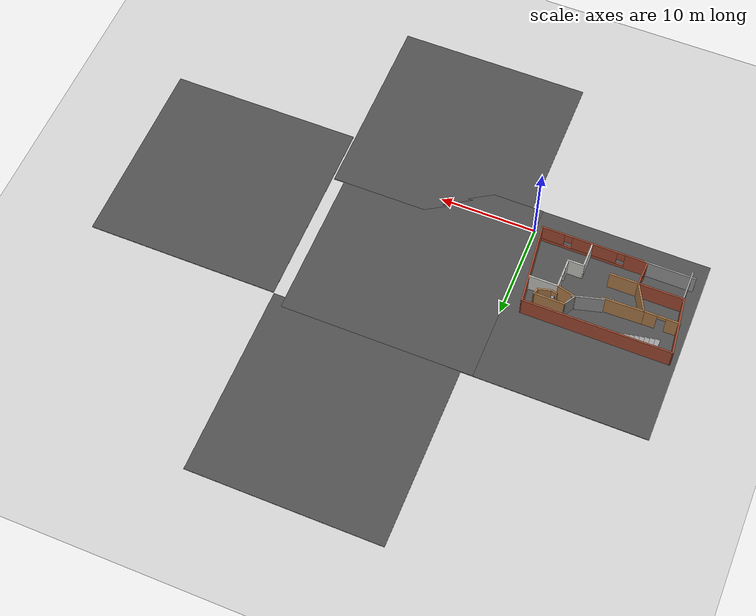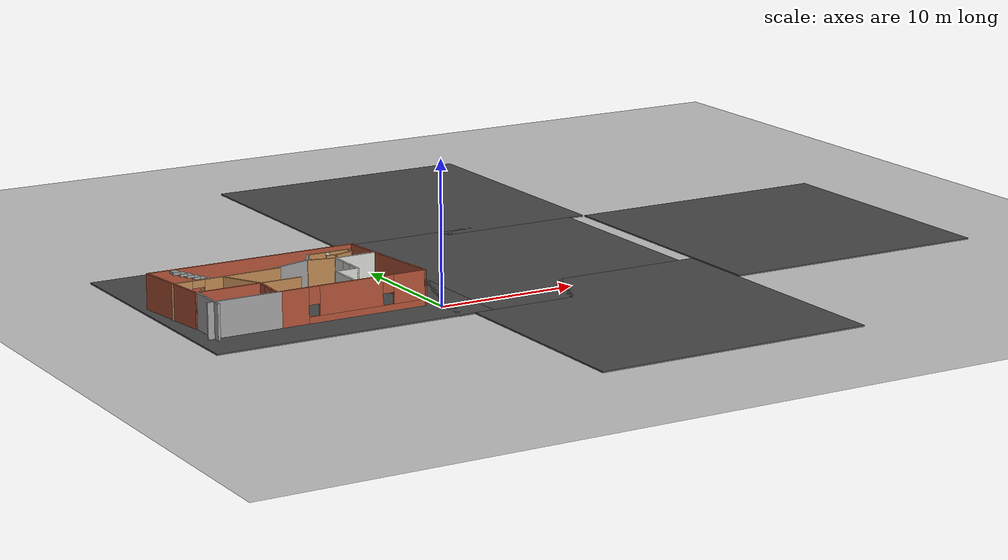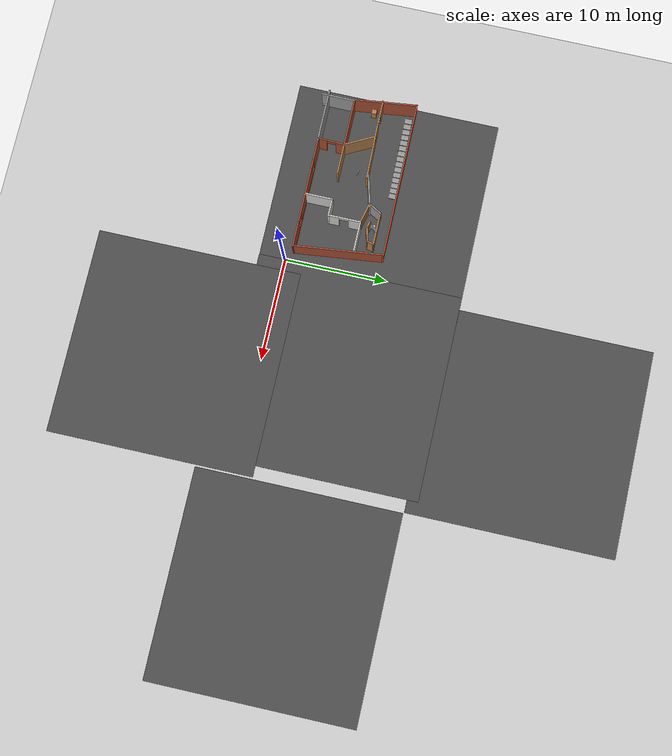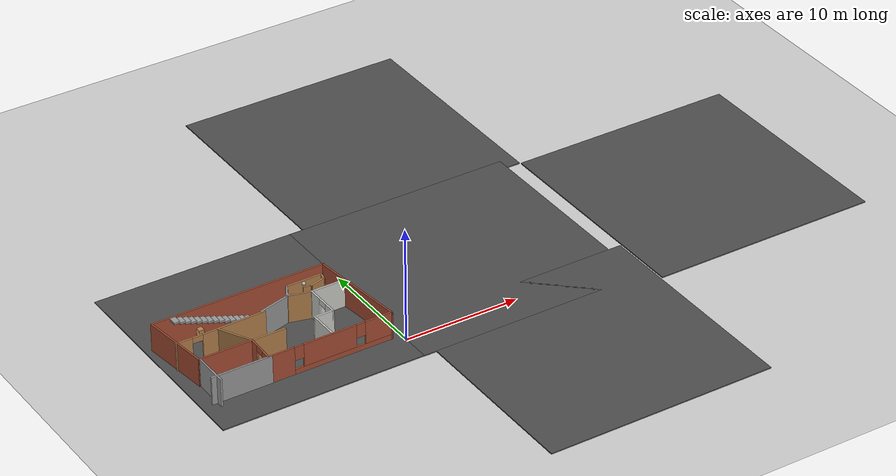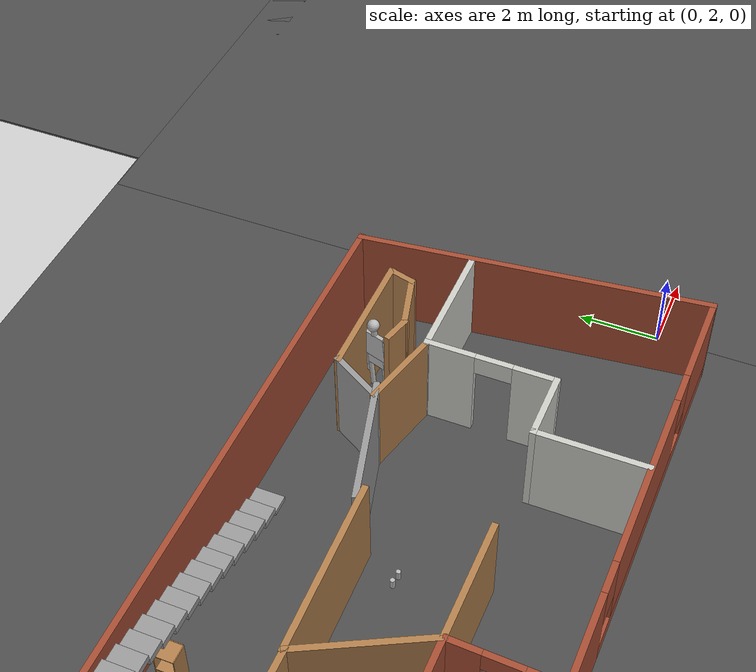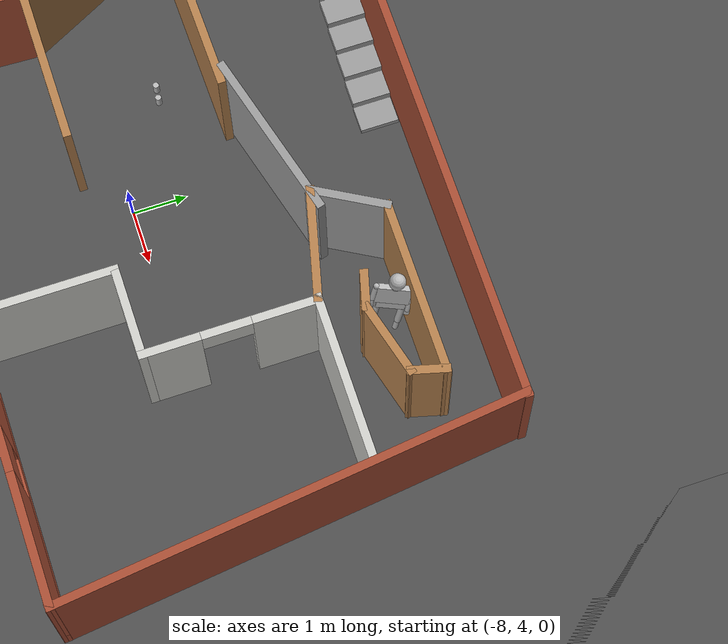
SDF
<sdf version="1.7">
 <world name="default">
  <light name="sun" type="directional">
   <pose>0 0 10 0 -0 0</pose>
   <diffuse>0.8 0.8 0.8 1</diffuse>
   <specular>0.2 0.2 0.2 1</specular>
   <attenuation>
    <range>1000</range>
    <constant>0.9</constant>
    <linear>0.01</linear>
    <quadratic>0.001</quadratic>
   </attenuation>
   <direction>-0.5 0.1 -0.9</direction>
   <spot><inner_angle>0</inner_angle><outer_angle>0</outer_angle><falloff>0</falloff></spot>
  </light>
  <model name="ground_plane">
   <static>1</static>
   <link name="link">
    <collision name="collision">
     <geometry><plane><normal>0 0 1</normal><size>100 100</size></plane></geometry>
     <surface><friction><ode><mu>100</mu><mu2>50</mu2></ode></friction></surface>
    </collision>
    <visual name="visual">
     <cast_shadows>0</cast_shadows>
     <geometry><plane><normal>0 0 1</normal><size>100 100</size></plane></geometry>
     <material>
      <script><uri>file://media/materials/scripts/gazebo.material</uri><name>Gazebo/Grey</name></script>
     </material>
    </visual>
   </link>
  </model>
  <gravity>0 0 -9.8</gravity>
  <magnetic_field>6e-06 2.3e-05 -4.2e-05</magnetic_field>
  <atmosphere type="adiabatic"/>
  <physics type="ode">
   <max_step_size>0.001</max_step_size>
   <real_time_factor>1</real_time_factor>
   <real_time_update_rate>1000</real_time_update_rate>
  </physics>
  <scene><ambient>0.4 0.4 0.4 1</ambient><background>0.7 0.7 0.7 1</background><shadows>1</shadows></scene>
  <audio><device>default</device></audio>
  <spherical_coordinates>
   <surface_model>EARTH_WGS84</surface_model>
   <latitude_deg>0</latitude_deg>
   <longitude_deg>0</longitude_deg>
   <elevation>0</elevation>
   <heading_deg>0</heading_deg>
  </spherical_coordinates>
  <model name="asphalt_plane">
   <static>1</static>
   <link name="link">
    <collision name="collision"><geometry><box><size>20 20 0.1</size></box></geometry></collision>
    <visual name="visual">
     <cast_shadows>0</cast_shadows>
     <geometry><box><size>20 20 0.1</size></box></geometry>
     <material>
      <script>
       <uri>model://asphalt_plane/materials/scripts</uri>
       <uri>model://asphalt_plane/materials/textures</uri>
       <name>vrc/asphalt</name>
      </script>
     </material>
    </visual>
   </link>
   <pose>9.99412 7.45899 0 0 -0 0</pose>
  </model>
  <model name="asphalt_plane_clone">
   <static>1</static>
   <link name="link">
    <collision name="collision"><geometry><box><size>20 20 0.1</size></box></geometry></collision>
    <visual name="visual">
     <cast_shadows>0</cast_shadows>
     <geometry><box><size>20 20 0.1</size></box></geometry>
     <material>
      <script>
       <uri>model://asphalt_plane/materials/scripts</uri>
       <uri>model://asphalt_plane/materials/textures</uri>
       <name>vrc/asphalt</name>
      </script>
     </material>
    </visual>
   </link>
   <pose>-7.54692 7.47993 0 0 -0 0</pose>
  </model>
  <model name="asphalt_plane_clone_0">
   <static>1</static>
   <link name="link">
    <collision name="collision"><geometry><box><size>20 20 0.1</size></box></geometry></collision>
    <visual name="visual">
     <cast_shadows>0</cast_shadows>
     <geometry><box><size>20 20 0.1</size></box></geometry>
     <material>
      <script>
       <uri>model://asphalt_plane/materials/scripts</uri>
       <uri>model://asphalt_plane/materials/textures</uri>
       <name>vrc/asphalt</name>
      </script>
     </material>
    </visual>
   </link>
   <pose>11.0922 -8.18214 0 0 -0 0</pose>
  </model>
  <model name="asphalt_plane_clone_1">
   <static>1</static>
   <link name="link">
    <collision name="collision"><geometry><box><size>20 20 0.1</size></box></geometry></collision>
    <visual name="visual">
     <cast_shadows>0</cast_shadows>
     <geometry><box><size>20 20 0.1</size></box></geometry>
     <material>
      <script>
       <uri>model://asphalt_plane/materials/scripts</uri>
       <uri>model://asphalt_plane/materials/textures</uri>
       <name>vrc/asphalt</name>
      </script>
     </material>
    </visual>
   </link>
   <pose>11.2066 26.3946 0 0 -0 0</pose>
  </model>
  <model name="asphalt_plane_clone_2">
   <static>1</static>
   <link name="link">
    <collision name="collision"><geometry><box><size>20 20 0.1</size></box></geometry></collision>
    <visual name="visual">
     <cast_shadows>0</cast_shadows>
     <geometry><box><size>20 20 0.1</size></box></geometry>
     <material>
      <script>
       <uri>model://asphalt_plane/materials/scripts</uri>
       <uri>model://asphalt_plane/materials/textures</uri>
       <name>vrc/asphalt</name>
      </script>
     </material>
    </visual>
   </link>
   <pose>31.2905 6.30185 0 0 -0 0</pose>
  </model>
  <model name="wonky_house">
   <pose>-8.51081 4.66291 0 0 -0 0</pose>
   <link name="Stairs_0">
    <visual name="Stairs_0_Visual_0">
     <pose>0.105992 4.11829 0.083333 0 -0 -1.5708</pose>
     <geometry><box><size>0.71857 0.484275 0.166667</size></box></geometry>
     <material>
      <script><uri>file://media/materials/scripts/gazebo.material</uri><name>Gazebo/Grey</name></script>
      <ambient>1 1 1 1</ambient>
     </material>
     <meta><layer>0</layer></meta>
    </visual>
    <collision name="Stairs_0_Collision_0">
     <geometry><box><size>0.71857 0.484275 0.166667</size></box></geometry>
     <pose>0.105992 4.11829 0.083333 0 -0 -1.5708</pose>
    </collision>
    <visual name="Stairs_0_Visual_1">
     <pose>-0.378284 4.11828 0.25 0 -0 -1.5708</pose>
     <geometry><box><size>0.71857 0.484275 0.166667</size></box></geometry>
     <material>
      <script><uri>file://media/materials/scripts/gazebo.material</uri><name>Gazebo/Grey</name></script>
      <ambient>1 1 1 1</ambient>
     </material>
     <meta><layer>0</layer></meta>
    </visual>
    <collision name="Stairs_0_Collision_1">
     <geometry><box><size>0.71857 0.484275 0.166667</size></box></geometry>
     <pose>-0.378284 4.11828 0.25 0 -0 -1.5708</pose>
    </collision>
    <visual name="Stairs_0_Visual_2">
     <pose>-0.862558 4.11828 0.416667 0 -0 -1.5708</pose>
     <geometry><box><size>0.71857 0.484275 0.166667</size></box></geometry>
     <material>
      <script><uri>file://media/materials/scripts/gazebo.material</uri><name>Gazebo/Grey</name></script>
      <ambient>1 1 1 1</ambient>
     </material>
     <meta><layer>0</layer></meta>
    </visual>
    <collision name="Stairs_0_Collision_2">
     <geometry><box><size>0.71857 0.484275 0.166667</size></box></geometry>
     <pose>-0.862558 4.11828 0.416667 0 -0 -1.5708</pose>
    </collision>
    <visual name="Stairs_0_Visual_3">
     <pose>-1.34683 4.11829 0.583333 0 -0 -1.5708</pose>
     <geometry><box><size>0.71857 0.484275 0.166667</size></box></geometry>
     <material>
      <script><uri>file://media/materials/scripts/gazebo.material</uri><name>Gazebo/Grey</name></script>
      <ambient>1 1 1 1</ambient>
     </material>
     <meta><layer>0</layer></meta>
    </visual>
    <collision name="Stairs_0_Collision_3">
     <geometry><box><size>0.71857 0.484275 0.166667</size></box></geometry>
     <pose>-1.34683 4.11829 0.583333 0 -0 -1.5708</pose>
    </collision>
    <visual name="Stairs_0_Visual_4">
     <pose>-1.83111 4.11829 0.75 0 -0 -1.5708</pose>
     <geometry><box><size>0.71857 0.484275 0.166667</size></box></geometry>
     <material>
      <script><uri>file://media/materials/scripts/gazebo.material</uri><name>Gazebo/Grey</name></script>
      <ambient>1 1 1 1</ambient>
     </material>
     <meta><layer>0</layer></meta>
    </visual>
    <collision name="Stairs_0_Collision_4">
     <geometry><box><size>0.71857 0.484275 0.166667</size></box></geometry>
     <pose>-1.83111 4.11829 0.75 0 -0 -1.5708</pose>
    </collision>
    <visual name="Stairs_0_Visual_5">
     <pose>-2.31538 4.11829 0.916667 0 -0 -1.5708</pose>
     <geometry><box><size>0.71857 0.484275 0.166667</size></box></geometry>
     <material>
      <script><uri>file://media/materials/scripts/gazebo.material</uri><name>Gazebo/Grey</name></script>
      <ambient>1 1 1 1</ambient>
     </material>
     <meta><layer>0</layer></meta>
    </visual>
    <collision name="Stairs_0_Collision_5">
     <geometry><box><size>0.71857 0.484275 0.166667</size></box></geometry>
     <pose>-2.31538 4.11829 0.916667 0 -0 -1.5708</pose>
    </collision>
    <visual name="Stairs_0_Visual_6">
     <pose>-2.79966 4.11829 1.08333 0 -0 -1.5708</pose>
     <geometry><box><size>0.71857 0.484275 0.166667</size></box></geometry>
     <material>
      <script><uri>file://media/materials/scripts/gazebo.material</uri><name>Gazebo/Grey</name></script>
      <ambient>1 1 1 1</ambient>
     </material>
     <meta><layer>0</layer></meta>
    </visual>
    <collision name="Stairs_0_Collision_6">
     <geometry><box><size>0.71857 0.484275 0.166667</size></box></geometry>
     <pose>-2.79966 4.11829 1.08333 0 -0 -1.5708</pose>
    </collision>
    <visual name="Stairs_0_Visual_7">
     <pose>-3.28394 4.11829 1.25 0 -0 -1.5708</pose>
     <geometry><box><size>0.71857 0.484275 0.166667</size></box></geometry>
     <material>
      <script><uri>file://media/materials/scripts/gazebo.material</uri><name>Gazebo/Grey</name></script>
      <ambient>1 1 1 1</ambient>
     </material>
     <meta><layer>0</layer></meta>
    </visual>
    <collision name="Stairs_0_Collision_7">
     <geometry><box><size>0.71857 0.484275 0.166667</size></box></geometry>
     <pose>-3.28394 4.11829 1.25 0 -0 -1.5708</pose>
    </collision>
    <visual name="Stairs_0_Visual_8">
     <pose>-3.76821 4.11829 1.41667 0 -0 -1.5708</pose>
     <geometry><box><size>0.71857 0.484275 0.166667</size></box></geometry>
     <material>
      <script><uri>file://media/materials/scripts/gazebo.material</uri><name>Gazebo/Grey</name></script>
      <ambient>1 1 1 1</ambient>
     </material>
     <meta><layer>0</layer></meta>
    </visual>
    <collision name="Stairs_0_Collision_8">
     <geometry><box><size>0.71857 0.484275 0.166667</size></box></geometry>
     <pose>-3.76821 4.11829 1.41667 0 -0 -1.5708</pose>
    </collision>
    <visual name="Stairs_0_Visual_9">
     <pose>-4.25249 4.11829 1.58333 0 -0 -1.5708</pose>
     <geometry><box><size>0.71857 0.484275 0.166667</size></box></geometry>
     <material>
      <script><uri>file://media/materials/scripts/gazebo.material</uri><name>Gazebo/Grey</name></script>
      <ambient>1 1 1 1</ambient>
     </material>
     <meta><layer>0</layer></meta>
    </visual>
    <collision name="Stairs_0_Collision_9">
     <geometry><box><size>0.71857 0.484275 0.166667</size></box></geometry>
     <pose>-4.25249 4.11829 1.58333 0 -0 -1.5708</pose>
    </collision>
    <visual name="Stairs_0_Visual_10">
     <pose>-4.73676 4.11829 1.75 0 -0 -1.5708</pose>
     <geometry><box><size>0.71857 0.484275 0.166667</size></box></geometry>
     <material>
      <script><uri>file://media/materials/scripts/gazebo.material</uri><name>Gazebo/Grey</name></script>
      <ambient>1 1 1 1</ambient>
     </material>
     <meta><layer>0</layer></meta>
    </visual>
    <collision name="Stairs_0_Collision_10">
     <geometry><box><size>0.71857 0.484275 0.166667</size></box></geometry>
     <pose>-4.73676 4.11829 1.75 0 -0 -1.5708</pose>
    </collision>
    <visual name="Stairs_0_Visual_11">
     <pose>-5.22104 4.11829 1.91667 0 -0 -1.5708</pose>
     <geometry><box><size>0.71857 0.484275 0.166667</size></box></geometry>
     <material>
      <script><uri>file://media/materials/scripts/gazebo.material</uri><name>Gazebo/Grey</name></script>
      <ambient>1 1 1 1</ambient>
     </material>
     <meta><layer>0</layer></meta>
    </visual>
    <collision name="Stairs_0_Collision_11">
     <geometry><box><size>0.71857 0.484275 0.166667</size></box></geometry>
     <pose>-5.22104 4.11829 1.91667 0 -0 -1.5708</pose>
    </collision>
    <visual name="Stairs_0_Visual_12">
     <pose>-5.70531 4.11829 2.08333 0 -0 -1.5708</pose>
     <geometry><box><size>0.71857 0.484275 0.166667</size></box></geometry>
     <material>
      <script><uri>file://media/materials/scripts/gazebo.material</uri><name>Gazebo/Grey</name></script>
      <ambient>1 1 1 1</ambient>
     </material>
     <meta><layer>0</layer></meta>
    </visual>
    <collision name="Stairs_0_Collision_12">
     <geometry><box><size>0.71857 0.484275 0.166667</size></box></geometry>
     <pose>-5.70531 4.11829 2.08333 0 -0 -1.5708</pose>
    </collision>
    <visual name="Stairs_0_Visual_13">
     <pose>-6.18959 4.11829 2.25 0 -0 -1.5708</pose>
     <geometry><box><size>0.71857 0.484275 0.166667</size></box></geometry>
     <material>
      <script><uri>file://media/materials/scripts/gazebo.material</uri><name>Gazebo/Grey</name></script>
      <ambient>1 1 1 1</ambient>
     </material>
     <meta><layer>0</layer></meta>
    </visual>
    <collision name="Stairs_0_Collision_13">
     <geometry><box><size>0.71857 0.484275 0.166667</size></box></geometry>
     <pose>-6.18959 4.11829 2.25 0 -0 -1.5708</pose>
    </collision>
    <visual name="Stairs_0_Visual_14">
     <pose>-6.67386 4.11829 2.41667 0 -0 -1.5708</pose>
     <geometry><box><size>0.71857 0.484275 0.166667</size></box></geometry>
     <material>
      <script><uri>file://media/materials/scripts/gazebo.material</uri><name>Gazebo/Grey</name></script>
      <ambient>1 1 1 1</ambient>
     </material>
     <meta><layer>0</layer></meta>
    </visual>
    <collision name="Stairs_0_Collision_14">
     <geometry><box><size>0.71857 0.484275 0.166667</size></box></geometry>
     <pose>-6.67386 4.11829 2.41667 0 -0 -1.5708</pose>
    </collision>
   </link>
   <link name="Wall_16">
    <collision name="Wall_16_Collision">
     <geometry><box><size>15.25 0.15 2.5</size></box></geometry>
     <pose>0 0 1.25 0 -0 0</pose>
    </collision>
    <visual name="Wall_16_Visual">
     <pose>0 0 1.25 0 -0 0</pose>
     <geometry><box><size>15.25 0.15 2.5</size></box></geometry>
     <material>
      <script><uri>file://media/materials/scripts/gazebo.material</uri><name>Gazebo/Bricks</name></script>
      <ambient>1 1 1 1</ambient>
     </material>
     <meta><layer>0</layer></meta>
    </visual>
    <pose>-0.850794 4.57949 0 0 -0 3.14159</pose>
   </link>
   <link name="Wall_17">
    <collision name="Wall_17_Collision">
     <geometry><box><size>6.16543 0.15 2.5</size></box></geometry>
     <pose>0 0 1.25 0 -0 0</pose>
    </collision>
    <visual name="Wall_17_Visual">
     <pose>0 0 1.25 0 -0 0</pose>
     <geometry><box><size>6.16543 0.15 2.5</size></box></geometry>
     <material>
      <script><uri>file://media/materials/scripts/gazebo.material</uri><name>Gazebo/Bricks</name></script>
      <ambient>1 1 1 1</ambient>
     </material>
     <meta><layer>0</layer></meta>
    </visual>
    <pose>-8.06829 1.59329 0 0 -0 -1.45112</pose>
   </link>
   <link name="Wall_18">
    <collision name="Wall_18_Collision">
     <geometry><box><size>4.75 0.15 2.5</size></box></geometry>
     <pose>0 0 1.25 0 -0 0</pose>
    </collision>
    <visual name="Wall_18_Visual">
     <pose>0 0 1.25 0 -0 0</pose>
     <geometry><box><size>4.75 0.15 2.5</size></box></geometry>
     <material>
      <script><uri>file://media/materials/scripts/gazebo.material</uri><name>Gazebo/Bricks</name></script>
      <ambient>1 1 1 1</ambient>
     </material>
     <meta><layer>0</layer></meta>
    </visual>
    <pose>-5.40919 -1.39291 0 0 -0 0</pose>
   </link>
   <link name="Wall_21">
    <collision name="Wall_21_Collision">
     <geometry><box><size>3.2014 0.15 2.5</size></box></geometry>
     <pose>0 0 1.25 0 -0 0</pose>
    </collision>
    <visual name="Wall_21_Visual">
     <pose>0 0 1.25 0 -0 0</pose>
     <geometry><box><size>3.2014 0.15 2.5</size></box></geometry>
     <material>
      <script><uri>file://media/materials/scripts/gazebo.material</uri><name>Gazebo/Wood</name></script>
      <ambient>1 1 1 1</ambient>
     </material>
     <meta><layer>0</layer></meta>
    </visual>
    <pose>-3.81409 -0.039815 0 0 -0 2.05107</pose>
   </link>
   <link name="Wall_22">
    <pose>-6.319 1.31328 0 0 -0 3.14159</pose>
    <visual name="Wall_22_Visual_0">
     <pose>-1.16791 0 1.25 0 -0 0</pose>
     <geometry><box><size>1.41417 0.15 2.5</size></box></geometry>
     <material>
      <script><uri>file://media/materials/scripts/gazebo.material</uri><name>Gazebo/Wood</name></script>
      <ambient>1 1 1 1</ambient>
     </material>
     <meta><layer>0</layer></meta>
    </visual>
    <collision name="Wall_22_Collision_0">
     <geometry><box><size>1.41417 0.15 2.5</size></box></geometry>
     <pose>-1.16791 0 1.25 0 -0 0</pose>
    </collision>
    <visual name="Wall_22_Visual_1">
     <pose>1.15709 0 1.25 0 -0 0</pose>
     <geometry><box><size>1.43583 0.15 2.5</size></box></geometry>
     <material>
      <script><uri>file://media/materials/scripts/gazebo.material</uri><name>Gazebo/Wood</name></script>
      <ambient>1 1 1 1</ambient>
     </material>
     <meta><layer>0</layer></meta>
    </visual>
    <collision name="Wall_22_Collision_1">
     <geometry><box><size>1.43583 0.15 2.5</size></box></geometry>
     <pose>1.15709 0 1.25 0 -0 0</pose>
    </collision>
    <visual name="Wall_22_Visual_2">
     <pose>-0.010826 0 2.25 0 -0 0</pose>
     <geometry><box><size>0.9 0.15 0.5</size></box></geometry>
     <material>
      <script><uri>file://media/materials/scripts/gazebo.material</uri><name>Gazebo/Wood</name></script>
      <ambient>1 1 1 1</ambient>
     </material>
     <meta><layer>0</layer></meta>
    </visual>
    <collision name="Wall_22_Collision_2">
     <geometry><box><size>0.9 0.15 0.5</size></box></geometry>
     <pose>-0.010826 0 2.25 0 -0 0</pose>
    </collision>
   </link>
   <link name="Wall_24">
    <pose>-3.15919 -2.66791 0 0 -0 1.5316</pose>
    <visual name="Wall_24_Visual_0">
     <pose>-0.891327 0 1.25 0 -0 0</pose>
     <geometry><box><size>0.919306 0.15 2.5</size></box></geometry>
     <material>
      <script><uri>file://media/materials/scripts/gazebo.material</uri><name>Gazebo/Bricks</name></script>
      <ambient>1 1 1 1</ambient>
     </material>
     <meta><layer>0</layer></meta>
    </visual>
    <collision name="Wall_24_Collision_0">
     <geometry><box><size>0.919306 0.15 2.5</size></box></geometry>
     <pose>-0.891327 0 1.25 0 -0 0</pose>
    </collision>
    <visual name="Wall_24_Visual_1">
     <pose>0.909653 0 1.25 0 -0 0</pose>
     <geometry><box><size>0.882654 0.15 2.5</size></box></geometry>
     <material>
      <script><uri>file://media/materials/scripts/gazebo.material</uri><name>Gazebo/Bricks</name></script>
      <ambient>1 1 1 1</ambient>
     </material>
     <meta><layer>0</layer></meta>
    </visual>
    <collision name="Wall_24_Collision_1">
     <geometry><box><size>0.882654 0.15 2.5</size></box></geometry>
     <pose>0.909653 0 1.25 0 -0 0</pose>
    </collision>
    <visual name="Wall_24_Visual_2">
     <pose>0.018326 0 2.25 0 -0 0</pose>
     <geometry><box><size>0.9 0.15 0.5</size></box></geometry>
     <material>
      <script><uri>file://media/materials/scripts/gazebo.material</uri><name>Gazebo/Bricks</name></script>
      <ambient>1 1 1 1</ambient>
     </material>
     <meta><layer>0</layer></meta>
    </visual>
    <collision name="Wall_24_Collision_2">
     <geometry><box><size>0.9 0.15 0.5</size></box></geometry>
     <pose>0.018326 0 2.25 0 -0 0</pose>
    </collision>
   </link>
   <link name="Wall_27">
    <collision name="Wall_27_Collision">
     <geometry><box><size>8.72722 0.15 2.5</size></box></geometry>
     <pose>0 0 1.25 0 -0 0</pose>
    </collision>
    <visual name="Wall_27_Visual">
     <pose>0 0 1.25 0 -0 0</pose>
     <geometry><box><size>8.72722 0.15 2.5</size></box></geometry>
     <material>
      <script><uri>file://media/materials/scripts/gazebo.material</uri><name>Gazebo/Bricks</name></script>
      <ambient>1 1 1 1</ambient>
     </material>
     <meta><layer>0</layer></meta>
    </visual>
    <pose>7.15671 0.318291 0 0 -0 1.68392</pose>
   </link>
   <link name="Wall_29">
    <collision name="Wall_29_Collision">
     <geometry><box><size>3 0.15 2.5</size></box></geometry>
     <pose>0 0 1.25 0 -0 0</pose>
    </collision>
    <visual name="Wall_29_Visual">
     <pose>0 0 1.25 0 -0 0</pose>
     <geometry><box><size>3 0.15 2.5</size></box></geometry>
     <material>
      <script><uri>file://media/materials/scripts/gazebo.material</uri><name>Gazebo/CeilingTiled</name></script>
      <ambient>1 1 1 1</ambient>
     </material>
     <meta><layer>0</layer></meta>
    </visual>
    <pose>5.42135 1.78856 0 0 -0 3.14159</pose>
   </link>
   <link name="Wall_30">
    <pose>4.02295 0.238559 0 0 -0 -1.5708</pose>
    <visual name="Wall_30_Visual_0">
     <pose>-1.00119 0 1.25 0 -0 0</pose>
     <geometry><box><size>1.24761 0.15 2.5</size></box></geometry>
     <material>
      <script><uri>file://media/materials/scripts/gazebo.material</uri><name>Gazebo/CeilingTiled</name></script>
      <ambient>1 1 1 1</ambient>
     </material>
     <meta><layer>0</layer></meta>
    </visual>
    <collision name="Wall_30_Collision_0">
     <geometry><box><size>1.24761 0.15 2.5</size></box></geometry>
     <pose>-1.00119 0 1.25 0 -0 0</pose>
    </collision>
    <visual name="Wall_30_Visual_1">
     <pose>1.07381 0 1.25 0 -0 0</pose>
     <geometry><box><size>1.10239 0.15 2.5</size></box></geometry>
     <material>
      <script><uri>file://media/materials/scripts/gazebo.material</uri><name>Gazebo/CeilingTiled</name></script>
      <ambient>1 1 1 1</ambient>
     </material>
     <meta><layer>0</layer></meta>
    </visual>
    <collision name="Wall_30_Collision_1">
     <geometry><box><size>1.10239 0.15 2.5</size></box></geometry>
     <pose>1.07381 0 1.25 0 -0 0</pose>
    </collision>
    <visual name="Wall_30_Visual_2">
     <pose>0.072612 0 2.25 0 -0 0</pose>
     <geometry><box><size>0.9 0.15 0.5</size></box></geometry>
     <material>
      <script><uri>file://media/materials/scripts/gazebo.material</uri><name>Gazebo/CeilingTiled</name></script>
      <ambient>1 1 1 1</ambient>
     </material>
     <meta><layer>0</layer></meta>
    </visual>
    <collision name="Wall_30_Collision_2">
     <geometry><box><size>0.9 0.15 0.5</size></box></geometry>
     <pose>0.072612 0 2.25 0 -0 0</pose>
    </collision>
   </link>
   <link name="Wall_32">
    <collision name="Wall_32_Collision">
     <geometry><box><size>2.11559 0.15 2.5</size></box></geometry>
     <pose>0 0 1.25 0 -0 0</pose>
    </collision>
    <visual name="Wall_32_Visual">
     <pose>0 0 1.25 0 -0 0</pose>
     <geometry><box><size>2.11559 0.15 2.5</size></box></geometry>
     <material>
      <script><uri>file://media/materials/scripts/gazebo.material</uri><name>Gazebo/Wood</name></script>
      <ambient>1 1 1 1</ambient>
     </material>
     <meta><layer>0</layer></meta>
    </visual>
    <pose>3.04309 2.02766 0 0 -0 2.89584</pose>
   </link>
   <link name="Wall_34">
    <collision name="Wall_34_Collision">
     <geometry><box><size>4.28757 0.15 2.5</size></box></geometry>
     <pose>0 0 1.25 0 -0 0</pose>
    </collision>
    <visual name="Wall_34_Visual">
     <pose>0 0 1.25 0 -0 0</pose>
     <geometry><box><size>4.28757 0.15 2.5</size></box></geometry>
     <material>
      <script><uri>file://media/materials/scripts/gazebo.material</uri><name>Gazebo/Wood</name></script>
      <ambient>1 1 1 1</ambient>
     </material>
     <meta><layer>0</layer></meta>
    </visual>
    <pose>-2.45075 1.38707 0 0 -0 -3.11878</pose>
   </link>
   <link name="Wall_36">
    <collision name="Wall_36_Collision">
     <geometry><box><size>3 0.15 2.5</size></box></geometry>
     <pose>0 0 1.25 0 -0 0</pose>
    </collision>
    <visual name="Wall_36_Visual">
     <pose>0 0 1.25 0 -0 0</pose>
     <geometry><box><size>3 0.15 2.5</size></box></geometry>
     <material>
      <script><uri>file://media/materials/scripts/gazebo.material</uri><name>Gazebo/Wood</name></script>
      <ambient>1 1 1 1</ambient>
     </material>
     <meta><layer>0</layer></meta>
    </visual>
    <pose>-1.68419 -1.39291 0 0 -0 0</pose>
   </link>
   <link name="Wall_38">
    <collision name="Wall_38_Collision">
     <geometry><box><size>1.75 0.15 2.5</size></box></geometry>
     <pose>0 0 1.25 0 -0 0</pose>
    </collision>
    <visual name="Wall_38_Visual">
     <pose>0 0 1.25 0 -0 0</pose>
     <geometry><box><size>1.75 0.15 2.5</size></box></geometry>
     <material>
      <script><uri>file://media/materials/scripts/gazebo.material</uri><name>Gazebo/CeilingTiled</name></script>
      <ambient>1 1 1 1</ambient>
     </material>
     <meta><layer>0</layer></meta>
    </visual>
    <pose>3.22295 -1.31144 0 0 -0 3.14159</pose>
   </link>
   <link name="Wall_39">
    <collision name="Wall_39_Collision">
     <geometry><box><size>2.75 0.15 2.5</size></box></geometry>
     <pose>0 0 1.25 0 -0 0</pose>
    </collision>
    <visual name="Wall_39_Visual">
     <pose>0 0 1.25 0 -0 0</pose>
     <geometry><box><size>2.75 0.15 2.5</size></box></geometry>
     <material>
      <script><uri>file://media/materials/scripts/gazebo.material</uri><name>Gazebo/CeilingTiled</name></script>
      <ambient>1 1 1 1</ambient>
     </material>
     <meta><layer>0</layer></meta>
    </visual>
    <pose>2.42295 -2.61144 0 0 -0 -1.5708</pose>
   </link>
   <link name="Wall_41">
    <collision name="Wall_41_Collision">
     <geometry><box><size>1.5 0.15 2.5</size></box></geometry>
     <pose>0 0 1.25 0 -0 0</pose>
    </collision>
    <visual name="Wall_41_Visual">
     <pose>0 0 1.25 0 -0 0</pose>
     <geometry><box><size>1.5 0.15 2.5</size></box></geometry>
     <material>
      <script><uri>file://media/materials/scripts/gazebo.material</uri><name>Gazebo/Grey</name></script>
      <ambient>1 1 1 1</ambient>
     </material>
     <meta><layer>0</layer></meta>
    </visual>
    <pose>2.42732 2.85133 0 0 -0 1.0472</pose>
   </link>
   <link name="Wall_42">
    <collision name="Wall_42_Collision">
     <geometry><box><size>3.25 0.15 2.5</size></box></geometry>
     <pose>0 0 1.25 0 -0 0</pose>
    </collision>
    <visual name="Wall_42_Visual">
     <pose>0 0 1.25 0 -0 0</pose>
     <geometry><box><size>3.25 0.15 2.5</size></box></geometry>
     <material>
      <script><uri>file://media/materials/scripts/gazebo.material</uri><name>Gazebo/Wood</name></script>
      <ambient>1 1 1 1</ambient>
     </material>
     <meta><layer>0</layer></meta>
    </visual>
    <pose>4.31482 3.43589 0 0 -0 0</pose>
   </link>
   <link name="Wall_43">
    <collision name="Wall_43_Collision">
     <geometry><box><size>0.75 0.15 2.5</size></box></geometry>
     <pose>0 0 1.25 0 -0 0</pose>
    </collision>
    <visual name="Wall_43_Visual">
     <pose>0 0 1.25 0 -0 0</pose>
     <geometry><box><size>0.75 0.15 2.5</size></box></geometry>
     <material>
      <script><uri>file://media/materials/scripts/gazebo.material</uri><name>Gazebo/Wood</name></script>
      <ambient>1 1 1 1</ambient>
     </material>
     <meta><layer>0</layer></meta>
    </visual>
    <pose>5.78718 3.14612 0 0 -0 -1.8326</pose>
   </link>
   <link name="Wall_44">
    <collision name="Wall_44_Collision">
     <geometry><box><size>1.5 0.15 2.5</size></box></geometry>
     <pose>0 0 1.25 0 -0 0</pose>
    </collision>
    <visual name="Wall_44_Visual">
     <pose>0 0 1.25 0 -0 0</pose>
     <geometry><box><size>1.5 0.15 2.5</size></box></geometry>
     <material>
      <script><uri>file://media/materials/scripts/gazebo.material</uri><name>Gazebo/Wood</name></script>
      <ambient>1 1 1 1</ambient>
     </material>
     <meta><layer>0</layer></meta>
    </visual>
    <pose>5.05753 2.68163 0 0 -0 -2.87979</pose>
   </link>
   <link name="Wall_45">
    <collision name="Wall_45_Collision">
     <geometry><box><size>0.75 0.15 2.5</size></box></geometry>
     <pose>0 0 1.25 0 -0 0</pose>
    </collision>
    <visual name="Wall_45_Visual">
     <pose>0 0 1.25 0 -0 0</pose>
     <geometry><box><size>0.75 0.15 2.5</size></box></geometry>
     <material>
      <script><uri>file://media/materials/scripts/gazebo.material</uri><name>Gazebo/Wood</name></script>
      <ambient>1 1 1 1</ambient>
     </material>
     <meta><layer>0</layer></meta>
    </visual>
    <pose>4.11575 2.58458 0 0 -0 2.87979</pose>
   </link>
   <link name="Wall_8">
    <pose>2.21581 -3.94291 0 0 -0 0</pose>
    <visual name="Wall_8_Visual_0">
     <pose>-4.33496 0 1.25 0 -0 0</pose>
     <geometry><box><size>2.33007 0.15 2.5</size></box></geometry>
     <material>
      <script><uri>file://media/materials/scripts/gazebo.material</uri><name>Gazebo/Bricks</name></script>
      <ambient>1 1 1 1</ambient>
     </material>
     <meta><layer>0</layer></meta>
    </visual>
    <collision name="Wall_8_Collision_0">
     <geometry><box><size>2.33007 0.15 2.5</size></box></geometry>
     <pose>-4.33496 0 1.25 0 -0 0</pose>
    </collision>
    <visual name="Wall_8_Visual_1">
     <pose>1.16504 0 0.25 0 -0 0</pose>
     <geometry><box><size>8.66993 0.15 0.5</size></box></geometry>
     <material>
      <script><uri>file://media/materials/scripts/gazebo.material</uri><name>Gazebo/Bricks</name></script>
      <ambient>1 1 1 1</ambient>
     </material>
     <meta><layer>0</layer></meta>
    </visual>
    <collision name="Wall_8_Collision_1">
     <geometry><box><size>8.66993 0.15 0.5</size></box></geometry>
     <pose>1.16504 0 0.25 0 -0 0</pose>
    </collision>
    <visual name="Wall_8_Visual_2">
     <pose>-0.056709 0 1.5 0 -0 0</pose>
     <geometry><box><size>4.62644 0.15 2</size></box></geometry>
     <material>
      <script><uri>file://media/materials/scripts/gazebo.material</uri><name>Gazebo/Bricks</name></script>
      <ambient>1 1 1 1</ambient>
     </material>
     <meta><layer>0</layer></meta>
    </visual>
    <collision name="Wall_8_Collision_2">
     <geometry><box><size>4.62644 0.15 2</size></box></geometry>
     <pose>-0.056709 0 1.5 0 -0 0</pose>
    </collision>
    <visual name="Wall_8_Visual_3">
     <pose>4.27826 0 1.5 0 -0 0</pose>
     <geometry><box><size>2.44349 0.15 2</size></box></geometry>
     <material>
      <script><uri>file://media/materials/scripts/gazebo.material</uri><name>Gazebo/Bricks</name></script>
      <ambient>1 1 1 1</ambient>
     </material>
     <meta><layer>0</layer></meta>
    </visual>
    <collision name="Wall_8_Collision_3">
     <geometry><box><size>2.44349 0.15 2</size></box></geometry>
     <pose>4.27826 0 1.5 0 -0 0</pose>
    </collision>
    <visual name="Wall_8_Visual_4">
     <pose>-2.76993 0 1.9 0 -0 0</pose>
     <geometry><box><size>0.8 0.15 1.2</size></box></geometry>
     <material>
      <script><uri>file://media/materials/scripts/gazebo.material</uri><name>Gazebo/Bricks</name></script>
      <ambient>1 1 1 1</ambient>
     </material>
     <meta><layer>0</layer></meta>
    </visual>
    <collision name="Wall_8_Collision_4">
     <geometry><box><size>0.8 0.15 1.2</size></box></geometry>
     <pose>-2.76993 0 1.9 0 -0 0</pose>
    </collision>
    <visual name="Wall_8_Visual_5">
     <pose>2.65651 0 1.9 0 -0 0</pose>
     <geometry><box><size>0.8 0.15 1.2</size></box></geometry>
     <material>
      <script><uri>file://media/materials/scripts/gazebo.material</uri><name>Gazebo/Bricks</name></script>
      <ambient>1 1 1 1</ambient>
     </material>
     <meta><layer>0</layer></meta>
    </visual>
    <collision name="Wall_8_Collision_5">
     <geometry><box><size>0.8 0.15 1.2</size></box></geometry>
     <pose>2.65651 0 1.9 0 -0 0</pose>
    </collision>
   </link>
   <static>1</static>
  </model>
  <model name="beer">
   <link name="link">
    <pose>0 0 0.115 0 -0 0</pose>
    <inertial>
     <mass>0.39</mass>
     <inertia><ixx>0.00058</ixx><ixy>0</ixy><ixz>0</ixz><iyy>0.00058</iyy><iyz>0</iyz><izz>0.00019</izz></inertia>
    </inertial>
    <collision name="collision">
     <geometry><cylinder><radius>0.055</radius><length>0.23</length></cylinder></geometry>
    </collision>
    <visual name="visual">
     <geometry><cylinder><radius>0.055</radius><length>0.23</length></cylinder></geometry>
     <material>
      <script>
       <uri>model://beer/materials/scripts</uri>
       <uri>model://beer/materials/textures</uri>
       <name>Beer/Diffuse</name>
      </script>
     </material>
    </visual>
   </link>
   <pose>-9.60015 5.04056 0.77499 -1e-06 2.6e-05 -0.006756</pose>
  </model>
  <model name="beer_0">
   <link name="link">
    <pose>0 0 0.115 0 -0 0</pose>
    <inertial>
     <mass>0.39</mass>
     <inertia><ixx>0.00058</ixx><ixy>0</ixy><ixz>0</ixz><iyy>0.00058</iyy><iyz>0</iyz><izz>0.00019</izz></inertia>
    </inertial>
    <collision name="collision">
     <geometry><cylinder><radius>0.055</radius><length>0.23</length></cylinder></geometry>
    </collision>
    <visual name="visual">
     <geometry><cylinder><radius>0.055</radius><length>0.23</length></cylinder></geometry>
     <material>
      <script>
       <uri>model://beer/materials/scripts</uri>
       <uri>model://beer/materials/textures</uri>
       <name>Beer/Diffuse</name>
      </script>
     </material>
    </visual>
   </link>
   <pose>-9.84611 5.07059 0.774992 -5e-06 -2.5e-05 0.002473</pose>
  </model>
  <model name="cabinet">
   <static>1</static>
   <link name="cabinet_bottom_plate">
    <inertial>
     <pose>0 0 -1 0 -0 0</pose>
     <inertia><ixx>2.05</ixx><ixy>0</ixy><ixz>0</ixz><iyy>2.05</iyy><iyz>0</iyz><izz>2.05</izz></inertia>
     <mass>25</mass>
    </inertial>
    <collision name="cabinet_bottom_plate_geom">
     <pose>0 0 0.01 0 -0 0</pose>
     <geometry><box><size>0.45 0.45 0.02</size></box></geometry>
    </collision>
    <visual name="cabinet_bottom_plate_geom_visual">
     <pose>0 0 0.01 0 -0 0</pose>
     <geometry><box><size>0.45 0.45 0.02</size></box></geometry>
     <material>
      <script><uri>file://media/materials/scripts/gazebo.material</uri><name>Gazebo/Wood</name></script>
     </material>
    </visual>
    <collision name="cabinet_bottom_plate_geom_cabinet_back_plate">
     <pose>0.235 0 0.51 0 -0 0</pose>
     <geometry><box><size>0.02 0.45 1.02</size></box></geometry>
    </collision>
    <visual name="cabinet_bottom_plate_geom_cabinet_back_plate_visual">
     <pose>0.235 0 0.51 0 -0 0</pose>
     <geometry><box><size>0.02 0.45 1.02</size></box></geometry>
     <material>
      <script><uri>file://media/materials/scripts/gazebo.material</uri><name>Gazebo/Wood</name></script>
     </material>
    </visual>
    <collision name="cabinet_bottom_plate_geom_cabinet_left_plate">
     <pose>0 0.235 0.51 0 -0 0</pose>
     <geometry><box><size>0.45 0.02 1.02</size></box></geometry>
    </collision>
    <visual name="cabinet_bottom_plate_geom_cabinet_left_plate_visual">
     <pose>0 0.235 0.51 0 -0 0</pose>
     <geometry><box><size>0.45 0.02 1.02</size></box></geometry>
     <material>
      <script><uri>file://media/materials/scripts/gazebo.material</uri><name>Gazebo/Wood</name></script>
     </material>
    </visual>
    <collision name="cabinet_bottom_plate_geom_cabinet_middle_plate">
     <pose>0 0 0.51 0 -0 0</pose>
     <geometry><box><size>0.45 0.45 0.02</size></box></geometry>
    </collision>
    <visual name="cabinet_bottom_plate_geom_cabinet_middle_plate_visual">
     <pose>0 0 0.51 0 -0 0</pose>
     <geometry><box><size>0.45 0.45 0.02</size></box></geometry>
     <material>
      <script><uri>file://media/materials/scripts/gazebo.material</uri><name>Gazebo/Wood</name></script>
     </material>
    </visual>
    <collision name="cabinet_bottom_plate_geom_cabinet_right_plate">
     <pose>0 -0.235 0.51 0 -0 0</pose>
     <geometry><box><size>0.45 0.02 1.02</size></box></geometry>
    </collision>
    <visual name="cabinet_bottom_plate_geom_cabinet_right_plate_visual">
     <pose>0 -0.235 0.51 0 -0 0</pose>
     <geometry><box><size>0.45 0.02 1.02</size></box></geometry>
     <material>
      <script><uri>file://media/materials/scripts/gazebo.material</uri><name>Gazebo/Wood</name></script>
     </material>
    </visual>
    <collision name="cabinet_bottom_plate_geom_cabinet_top_plate">
     <pose>0 0 1.01 0 -0 0</pose>
     <geometry><box><size>0.45 0.45 0.02</size></box></geometry>
    </collision>
    <visual name="cabinet_bottom_plate_geom_cabinet_top_plate_visual">
     <pose>0 0 1.01 0 -0 0</pose>
     <geometry><box><size>0.45 0.45 0.02</size></box></geometry>
     <material>
      <script><uri>file://media/materials/scripts/gazebo.material</uri><name>Gazebo/Wood</name></script>
     </material>
    </visual>
   </link>
   <pose>-13.1601 8.59059 0 0 -0 0</pose>
  </model>
  <model name="cabinet_0">
   <static>1</static>
   <link name="cabinet_bottom_plate">
    <inertial>
     <pose>0 0 -1 0 -0 0</pose>
     <inertia><ixx>2.05</ixx><ixy>0</ixy><ixz>0</ixz><iyy>2.05</iyy><iyz>0</iyz><izz>2.05</izz></inertia>
     <mass>25</mass>
    </inertial>
    <collision name="cabinet_bottom_plate_geom">
     <pose>0 0 0.01 0 -0 0</pose>
     <geometry><box><size>0.45 0.45 0.02</size></box></geometry>
    </collision>
    <visual name="cabinet_bottom_plate_geom_visual">
     <pose>0 0 0.01 0 -0 0</pose>
     <geometry><box><size>0.45 0.45 0.02</size></box></geometry>
     <material>
      <script><uri>file://media/materials/scripts/gazebo.material</uri><name>Gazebo/Wood</name></script>
     </material>
    </visual>
    <collision name="cabinet_bottom_plate_geom_cabinet_back_plate">
     <pose>0.235 0 0.51 0 -0 0</pose>
     <geometry><box><size>0.02 0.45 1.02</size></box></geometry>
    </collision>
    <visual name="cabinet_bottom_plate_geom_cabinet_back_plate_visual">
     <pose>0.235 0 0.51 0 -0 0</pose>
     <geometry><box><size>0.02 0.45 1.02</size></box></geometry>
     <material>
      <script><uri>file://media/materials/scripts/gazebo.material</uri><name>Gazebo/Wood</name></script>
     </material>
    </visual>
    <collision name="cabinet_bottom_plate_geom_cabinet_left_plate">
     <pose>0 0.235 0.51 0 -0 0</pose>
     <geometry><box><size>0.45 0.02 1.02</size></box></geometry>
    </collision>
    <visual name="cabinet_bottom_plate_geom_cabinet_left_plate_visual">
     <pose>0 0.235 0.51 0 -0 0</pose>
     <geometry><box><size>0.45 0.02 1.02</size></box></geometry>
     <material>
      <script><uri>file://media/materials/scripts/gazebo.material</uri><name>Gazebo/Wood</name></script>
     </material>
    </visual>
    <collision name="cabinet_bottom_plate_geom_cabinet_middle_plate">
     <pose>0 0 0.51 0 -0 0</pose>
     <geometry><box><size>0.45 0.45 0.02</size></box></geometry>
    </collision>
    <visual name="cabinet_bottom_plate_geom_cabinet_middle_plate_visual">
     <pose>0 0 0.51 0 -0 0</pose>
     <geometry><box><size>0.45 0.45 0.02</size></box></geometry>
     <material>
      <script><uri>file://media/materials/scripts/gazebo.material</uri><name>Gazebo/Wood</name></script>
     </material>
    </visual>
    <collision name="cabinet_bottom_plate_geom_cabinet_right_plate">
     <pose>0 -0.235 0.51 0 -0 0</pose>
     <geometry><box><size>0.45 0.02 1.02</size></box></geometry>
    </collision>
    <visual name="cabinet_bottom_plate_geom_cabinet_right_plate_visual">
     <pose>0 -0.235 0.51 0 -0 0</pose>
     <geometry><box><size>0.45 0.02 1.02</size></box></geometry>
     <material>
      <script><uri>file://media/materials/scripts/gazebo.material</uri><name>Gazebo/Wood</name></script>
     </material>
    </visual>
    <collision name="cabinet_bottom_plate_geom_cabinet_top_plate">
     <pose>0 0 1.01 0 -0 0</pose>
     <geometry><box><size>0.45 0.45 0.02</size></box></geometry>
    </collision>
    <visual name="cabinet_bottom_plate_geom_cabinet_top_plate_visual">
     <pose>0 0 1.01 0 -0 0</pose>
     <geometry><box><size>0.45 0.45 0.02</size></box></geometry>
     <material>
      <script><uri>file://media/materials/scripts/gazebo.material</uri><name>Gazebo/Wood</name></script>
     </material>
    </visual>
   </link>
   <pose>-16.1007 5.27311 0 0 -0 0</pose>
  </model>
  <model name="ragdoll">
   <pose>-4.44415 7.70545 1.16137 -0.107254 0.003522 -0.380616</pose>
   <link name="hip">
    <inertial>
     <inertia><ixx>0.1</ixx><ixy>0</ixy><ixz>0</ixz><iyy>0.1</iyy><iyz>0</iyz><izz>0.1</izz></inertia>
     <mass>10</mass>
    </inertial>
    <collision name="hip_geom">
     <pose>0 0 0.125 0 -0 0</pose>
     <geometry><box><size>0.1 0.5 0.25</size></box></geometry>
     <surface>
      <friction><ode><mu>-1</mu><mu2>-1</mu2><fdir1>0 0 0</fdir1><slip1>0</slip1><slip2>0</slip2></ode></friction>
      <bounce><restitution_coefficient>0</restitution_coefficient><threshold>100000</threshold></bounce>
      <contact>
       <ode>
        <soft_cfm>0</soft_cfm>
        <soft_erp>0.2</soft_erp>
        <kp>1e+12</kp>
        <kd>1</kd>
        <max_vel>0</max_vel>
        <min_depth>0.001</min_depth>
       </ode>
      </contact>
     </surface>
    </collision>
    <visual name="hip_geom_visual">
     <pose>0 0 0.125 0 -0 0</pose>
     <geometry><box><size>0.1 0.5 0.25</size></box></geometry>
    </visual>
    <gravity>0</gravity>
   </link>
   <link name="l_thigh_pan">
    <pose>0 0.22 0 0 -0 0</pose>
    <inertial>
     <inertia><ixx>0.01</ixx><ixy>0</ixy><ixz>0</ixz><iyy>0.01</iyy><iyz>0</iyz><izz>0.01</izz></inertia>
     <mass>1</mass>
    </inertial>
    <collision name="l_thigh_pan_geom">
     <pose>0 0 -0.03 0 -0 0</pose>
     <geometry><sphere><radius>0.06</radius></sphere></geometry>
     <surface>
      <friction><ode><mu>-1</mu><mu2>-1</mu2><fdir1>0 0 0</fdir1><slip1>0</slip1><slip2>0</slip2></ode></friction>
      <bounce><restitution_coefficient>0</restitution_coefficient><threshold>100000</threshold></bounce>
      <contact>
       <ode>
        <soft_cfm>0</soft_cfm>
        <soft_erp>0.2</soft_erp>
        <kp>1e+12</kp>
        <kd>1</kd>
        <max_vel>0</max_vel>
        <min_depth>0.001</min_depth>
       </ode>
      </contact>
     </surface>
    </collision>
    <visual name="l_thigh_pan_geom_visual">
     <pose>0 0 -0.03 0 -0 0</pose>
     <geometry><sphere><radius>0.06</radius></sphere></geometry>
    </visual>
    <gravity>0</gravity>
   </link>
   <link name="l_thigh_lift">
    <pose>0 0.22 0 0 -0 0</pose>
    <inertial>
     <inertia><ixx>0.05</ixx><ixy>0</ixy><ixz>0</ixz><iyy>0.05</iyy><iyz>0</iyz><izz>0.05</izz></inertia>
     <mass>5</mass>
    </inertial>
    <collision name="l_thigh_lift_geom">
     <pose>0 0 -0.35 0 -0 0</pose>
     <geometry><cylinder><radius>0.06</radius><length>0.7</length></cylinder></geometry>
     <surface>
      <friction><ode><mu>-1</mu><mu2>-1</mu2><fdir1>0 0 0</fdir1><slip1>0</slip1><slip2>0</slip2></ode></friction>
      <bounce><restitution_coefficient>0</restitution_coefficient><threshold>100000</threshold></bounce>
      <contact>
       <ode>
        <soft_cfm>0</soft_cfm>
        <soft_erp>0.2</soft_erp>
        <kp>1e+12</kp>
        <kd>1</kd>
        <max_vel>0</max_vel>
        <min_depth>0.001</min_depth>
       </ode>
      </contact>
     </surface>
    </collision>
    <visual name="l_thigh_lift_geom_visual">
     <pose>0 0 -0.35 0 -0 0</pose>
     <geometry><cylinder><radius>0.06</radius><length>0.7</length></cylinder></geometry>
    </visual>
    <gravity>0</gravity>
   </link>
   <link name="l_calf">
    <pose>0 0.22 -0.7 0 -0 0</pose>
    <inertial>
     <inertia><ixx>0.02</ixx><ixy>0</ixy><ixz>0</ixz><iyy>0.02</iyy><iyz>0</iyz><izz>0.02</izz></inertia>
     <mass>2</mass>
    </inertial>
    <collision name="l_calf_geom">
     <pose>0 0 -0.3 0 -0 0</pose>
     <geometry><cylinder><radius>0.05</radius><length>0.6</length></cylinder></geometry>
     <surface>
      <friction><ode><mu>-1</mu><mu2>-1</mu2><fdir1>0 0 0</fdir1><slip1>0</slip1><slip2>0</slip2></ode></friction>
      <bounce><restitution_coefficient>0</restitution_coefficient><threshold>100000</threshold></bounce>
      <contact>
       <ode>
        <soft_cfm>0</soft_cfm>
        <soft_erp>0.2</soft_erp>
        <kp>1e+12</kp>
        <kd>1</kd>
        <max_vel>0</max_vel>
        <min_depth>0.001</min_depth>
       </ode>
      </contact>
     </surface>
    </collision>
    <visual name="l_calf_geom_visual">
     <pose>0 0 -0.3 0 -0 0</pose>
     <geometry><cylinder><radius>0.05</radius><length>0.6</length></cylinder></geometry>
    </visual>
    <gravity>0</gravity>
   </link>
   <link name="l_ankle">
    <pose>0 0.22 -1.325 0 -0 0</pose>
    <inertial>
     <inertia><ixx>0.01</ixx><ixy>0</ixy><ixz>0</ixz><iyy>0.01</iyy><iyz>0</iyz><izz>0.01</izz></inertia>
     <mass>1</mass>
    </inertial>
    <collision name="l_ankle_geom">
     <geometry><sphere><radius>0.05</radius></sphere></geometry>
     <surface>
      <friction><ode><mu>-1</mu><mu2>-1</mu2><fdir1>0 0 0</fdir1><slip1>0</slip1><slip2>0</slip2></ode></friction>
      <bounce><restitution_coefficient>0</restitution_coefficient><threshold>100000</threshold></bounce>
      <contact>
       <ode>
        <soft_cfm>0</soft_cfm>
        <soft_erp>0.2</soft_erp>
        <kp>1e+12</kp>
        <kd>1</kd>
        <max_vel>0</max_vel>
        <min_depth>0.001</min_depth>
       </ode>
      </contact>
     </surface>
    </collision>
    <visual name="l_ankle_geom_visual"><geometry><sphere><radius>0.05</radius></sphere></geometry></visual>
    <gravity>0</gravity>
   </link>
   <link name="l_foot">
    <pose>0 0.22 -1.35 0 -0 0</pose>
    <inertial>
     <pose>0.1 0 0 0 -0 0</pose>
     <inertia><ixx>0.01</ixx><ixy>0</ixy><ixz>0</ixz><iyy>0.01</iyy><iyz>0</iyz><izz>0.01</izz></inertia>
     <mass>1</mass>
    </inertial>
    <collision name="l_foot_geom">
     <pose>0.1 0 -0.025 0 -0 0</pose>
     <geometry><box><size>0.2 0.03 0.05</size></box></geometry>
     <surface>
      <friction><ode><mu>-1</mu><mu2>-1</mu2><fdir1>0 0 0</fdir1><slip1>0</slip1><slip2>0</slip2></ode></friction>
      <bounce><restitution_coefficient>0</restitution_coefficient><threshold>100000</threshold></bounce>
      <contact>
       <ode>
        <soft_cfm>0</soft_cfm>
        <soft_erp>0.2</soft_erp>
        <kp>1e+12</kp>
        <kd>1</kd>
        <max_vel>0</max_vel>
        <min_depth>0.001</min_depth>
       </ode>
      </contact>
     </surface>
    </collision>
    <visual name="l_foot_geom_visual">
     <pose>0.1 0 -0.025 0 -0 0</pose>
     <geometry><box><size>0.2 0.03 0.05</size></box></geometry>
    </visual>
   </link>
   <link name="r_thigh_pan">
    <pose>0 -0.22 0 0 -0 0</pose>
    <inertial>
     <inertia><ixx>0.01</ixx><ixy>0</ixy><ixz>0</ixz><iyy>0.01</iyy><iyz>0</iyz><izz>0.01</izz></inertia>
     <mass>1</mass>
    </inertial>
    <collision name="r_thigh_pan_geom">
     <pose>0 0 -0.03 0 -0 0</pose>
     <geometry><sphere><radius>0.06</radius></sphere></geometry>
     <surface>
      <friction><ode><mu>-1</mu><mu2>-1</mu2><fdir1>0 0 0</fdir1><slip1>0</slip1><slip2>0</slip2></ode></friction>
      <bounce><restitution_coefficient>0</restitution_coefficient><threshold>100000</threshold></bounce>
      <contact>
       <ode>
        <soft_cfm>0</soft_cfm>
        <soft_erp>0.2</soft_erp>
        <kp>1e+12</kp>
        <kd>1</kd>
        <max_vel>0</max_vel>
        <min_depth>0.001</min_depth>
       </ode>
      </contact>
     </surface>
    </collision>
    <visual name="r_thigh_pan_geom_visual">
     <pose>0 0 -0.03 0 -0 0</pose>
     <geometry><sphere><radius>0.06</radius></sphere></geometry>
    </visual>
    <gravity>0</gravity>
   </link>
   <link name="r_thigh_lift">
    <pose>0 -0.22 0 0 -0 0</pose>
    <inertial>
     <inertia><ixx>0.05</ixx><ixy>0</ixy><ixz>0</ixz><iyy>0.05</iyy><iyz>0</iyz><izz>0.05</izz></inertia>
     <mass>5</mass>
    </inertial>
    <collision name="r_thigh_lift_geom">
     <pose>0 0 -0.35 0 -0 0</pose>
     <geometry><cylinder><radius>0.06</radius><length>0.7</length></cylinder></geometry>
     <surface>
      <friction><ode><mu>-1</mu><mu2>-1</mu2><fdir1>0 0 0</fdir1><slip1>0</slip1><slip2>0</slip2></ode></friction>
      <bounce><restitution_coefficient>0</restitution_coefficient><threshold>100000</threshold></bounce>
      <contact>
       <ode>
        <soft_cfm>0</soft_cfm>
        <soft_erp>0.2</soft_erp>
        <kp>1e+12</kp>
        <kd>1</kd>
        <max_vel>0</max_vel>
        <min_depth>0.001</min_depth>
       </ode>
      </contact>
     </surface>
    </collision>
    <visual name="r_thigh_lift_geom_visual">
     <pose>0 0 -0.35 0 -0 0</pose>
     <geometry><cylinder><radius>0.06</radius><length>0.7</length></cylinder></geometry>
    </visual>
    <gravity>0</gravity>
   </link>
   <link name="r_calf">
    <pose>0 -0.22 -0.7 0 -0 0</pose>
    <inertial>
     <inertia><ixx>0.02</ixx><ixy>0</ixy><ixz>0</ixz><iyy>0.02</iyy><iyz>0</iyz><izz>0.02</izz></inertia>
     <mass>2</mass>
    </inertial>
    <collision name="r_calf_geom">
     <pose>0 0 -0.3 0 -0 0</pose>
     <geometry><cylinder><radius>0.05</radius><length>0.6</length></cylinder></geometry>
     <surface>
      <friction><ode><mu>-1</mu><mu2>-1</mu2><fdir1>0 0 0</fdir1><slip1>0</slip1><slip2>0</slip2></ode></friction>
      <bounce><restitution_coefficient>0</restitution_coefficient><threshold>100000</threshold></bounce>
      <contact>
       <ode>
        <soft_cfm>0</soft_cfm>
        <soft_erp>0.2</soft_erp>
        <kp>1e+12</kp>
        <kd>1</kd>
        <max_vel>0</max_vel>
        <min_depth>0.001</min_depth>
       </ode>
      </contact>
     </surface>
    </collision>
    <visual name="r_calf_geom_visual">
     <pose>0 0 -0.3 0 -0 0</pose>
     <geometry><cylinder><radius>0.05</radius><length>0.6</length></cylinder></geometry>
    </visual>
    <gravity>0</gravity>
   </link>
   <link name="r_ankle">
    <pose>0 -0.22 -1.325 0 -0 0</pose>
    <inertial>
     <inertia><ixx>0.01</ixx><ixy>0</ixy><ixz>0</ixz><iyy>0.01</iyy><iyz>0</iyz><izz>0.01</izz></inertia>
     <mass>1</mass>
    </inertial>
    <collision name="r_ankle_geom">
     <geometry><sphere><radius>0.05</radius></sphere></geometry>
     <surface>
      <friction><ode><mu>-1</mu><mu2>-1</mu2><fdir1>0 0 0</fdir1><slip1>0</slip1><slip2>0</slip2></ode></friction>
      <bounce><restitution_coefficient>0</restitution_coefficient><threshold>100000</threshold></bounce>
      <contact>
       <ode>
        <soft_cfm>0</soft_cfm>
        <soft_erp>0.2</soft_erp>
        <kp>1e+12</kp>
        <kd>1</kd>
        <max_vel>0</max_vel>
        <min_depth>0.001</min_depth>
       </ode>
      </contact>
     </surface>
    </collision>
    <visual name="r_ankle_geom_visual"><geometry><sphere><radius>0.05</radius></sphere></geometry></visual>
    <gravity>0</gravity>
   </link>
   <link name="r_foot">
    <pose>0 -0.22 -1.35 0 -0 0</pose>
    <inertial>
     <pose>0.1 0 0 0 -0 0</pose>
     <inertia><ixx>0.01</ixx><ixy>0</ixy><ixz>0</ixz><iyy>0.01</iyy><iyz>0</iyz><izz>0.01</izz></inertia>
     <mass>1</mass>
    </inertial>
    <collision name="r_foot_geom">
     <pose>0.1 0 -0.025 0 -0 0</pose>
     <geometry><box><size>0.2 0.03 0.05</size></box></geometry>
     <surface>
      <friction><ode><mu>-1</mu><mu2>-1</mu2><fdir1>0 0 0</fdir1><slip1>0</slip1><slip2>0</slip2></ode></friction>
      <bounce><restitution_coefficient>0</restitution_coefficient><threshold>100000</threshold></bounce>
      <contact>
       <ode>
        <soft_cfm>0</soft_cfm>
        <soft_erp>0.2</soft_erp>
        <kp>1e+12</kp>
        <kd>1</kd>
        <max_vel>0</max_vel>
        <min_depth>0.001</min_depth>
       </ode>
      </contact>
     </surface>
    </collision>
    <visual name="r_foot_geom_visual">
     <pose>0.1 0 -0.025 0 -0 0</pose>
     <geometry><box><size>0.2 0.03 0.05</size></box></geometry>
    </visual>
   </link>
   <link name="torso">
    <pose>0 0 0.25 0 -0 0</pose>
    <inertial>
     <inertia><ixx>0.3</ixx><ixy>0</ixy><ixz>0</ixz><iyy>0.3</iyy><iyz>0</iyz><izz>0.3</izz></inertia>
     <mass>30</mass>
    </inertial>
    <collision name="torso_geom">
     <pose>0 0 0.35 0 -0 0</pose>
     <geometry><box><size>0.1 0.6 0.7</size></box></geometry>
     <surface>
      <friction><ode><mu>-1</mu><mu2>-1</mu2><fdir1>0 0 0</fdir1><slip1>0</slip1><slip2>0</slip2></ode></friction>
      <bounce><restitution_coefficient>0</restitution_coefficient><threshold>100000</threshold></bounce>
      <contact>
       <ode>
        <soft_cfm>0</soft_cfm>
        <soft_erp>0.2</soft_erp>
        <kp>1e+12</kp>
        <kd>1</kd>
        <max_vel>0</max_vel>
        <min_depth>0.001</min_depth>
       </ode>
      </contact>
     </surface>
    </collision>
    <visual name="torso_geom_visual">
     <pose>0 0 0.35 0 -0 0</pose>
     <geometry><box><size>0.1 0.6 0.7</size></box></geometry>
    </visual>
    <gravity>0</gravity>
   </link>
   <link name="l_shoulder">
    <pose>0 0.3275 0.9225 0 -0 0</pose>
    <inertial>
     <inertia><ixx>0.01</ixx><ixy>0</ixy><ixz>0</ixz><iyy>0.01</iyy><iyz>0</iyz><izz>0.01</izz></inertia>
     <mass>1</mass>
    </inertial>
    <collision name="l_shoulder_geom">
     <geometry><sphere><radius>0.055</radius></sphere></geometry>
     <surface>
      <friction><ode><mu>-1</mu><mu2>-1</mu2><fdir1>0 0 0</fdir1><slip1>0</slip1><slip2>0</slip2></ode></friction>
      <bounce><restitution_coefficient>0</restitution_coefficient><threshold>100000</threshold></bounce>
      <contact>
       <ode>
        <soft_cfm>0</soft_cfm>
        <soft_erp>0.2</soft_erp>
        <kp>1e+12</kp>
        <kd>1</kd>
        <max_vel>0</max_vel>
        <min_depth>0.001</min_depth>
       </ode>
      </contact>
     </surface>
    </collision>
    <visual name="l_shoulder_geom_visual"><geometry><sphere><radius>0.055</radius></sphere></geometry></visual>
    <gravity>0</gravity>
   </link>
   <link name="l_upper_arm">
    <pose>0 0.3275 0.9225 0 -0 0</pose>
    <inertial>
     <inertia><ixx>0.02</ixx><ixy>0</ixy><ixz>0</ixz><iyy>0.02</iyy><iyz>0</iyz><izz>0.02</izz></inertia>
     <mass>2</mass>
    </inertial>
    <collision name="l_upper_arm_geom">
     <pose>0 0 -0.3 0 -0 0</pose>
     <geometry><cylinder><radius>0.055</radius><length>0.6</length></cylinder></geometry>
     <surface>
      <friction><ode><mu>-1</mu><mu2>-1</mu2><fdir1>0 0 0</fdir1><slip1>0</slip1><slip2>0</slip2></ode></friction>
      <bounce><restitution_coefficient>0</restitution_coefficient><threshold>100000</threshold></bounce>
      <contact>
       <ode>
        <soft_cfm>0</soft_cfm>
        <soft_erp>0.2</soft_erp>
        <kp>1e+12</kp>
        <kd>1</kd>
        <max_vel>0</max_vel>
        <min_depth>0.001</min_depth>
       </ode>
      </contact>
     </surface>
    </collision>
    <visual name="l_upper_arm_geom_visual">
     <pose>0 0 -0.3 0 -0 0</pose>
     <geometry><cylinder><radius>0.055</radius><length>0.6</length></cylinder></geometry>
    </visual>
    <gravity>0</gravity>
   </link>
   <link name="l_forearm">
    <pose>0 0.3275 0.3225 0 -0 0</pose>
    <inertial>
     <inertia><ixx>0.01</ixx><ixy>0</ixy><ixz>0</ixz><iyy>0.01</iyy><iyz>0</iyz><izz>0.01</izz></inertia>
     <mass>1</mass>
    </inertial>
    <collision name="l_forearm_geom">
     <pose>0 0 -0.225 0 -0 0</pose>
     <geometry><cylinder><radius>0.05</radius><length>0.45</length></cylinder></geometry>
     <surface>
      <friction><ode><mu>-1</mu><mu2>-1</mu2><fdir1>0 0 0</fdir1><slip1>0</slip1><slip2>0</slip2></ode></friction>
      <bounce><restitution_coefficient>0</restitution_coefficient><threshold>100000</threshold></bounce>
      <contact>
       <ode>
        <soft_cfm>0</soft_cfm>
        <soft_erp>0.2</soft_erp>
        <kp>1e+12</kp>
        <kd>1</kd>
        <max_vel>0</max_vel>
        <min_depth>0.001</min_depth>
       </ode>
      </contact>
     </surface>
    </collision>
    <visual name="l_forearm_geom_visual">
     <pose>0 0 -0.225 0 -0 0</pose>
     <geometry><cylinder><radius>0.05</radius><length>0.45</length></cylinder></geometry>
    </visual>
    <gravity>0</gravity>
   </link>
   <link name="l_wrist">
    <pose>0 0.3275 -0.1425 0 -0 0</pose>
    <inertial>
     <inertia><ixx>0.01</ixx><ixy>0</ixy><ixz>0</ixz><iyy>0.01</iyy><iyz>0</iyz><izz>0.01</izz></inertia>
     <mass>1</mass>
    </inertial>
    <collision name="l_wrist_geom">
     <geometry><sphere><radius>0.03</radius></sphere></geometry>
     <surface>
      <friction><ode><mu>-1</mu><mu2>-1</mu2><fdir1>0 0 0</fdir1><slip1>0</slip1><slip2>0</slip2></ode></friction>
      <bounce><restitution_coefficient>0</restitution_coefficient><threshold>100000</threshold></bounce>
      <contact>
       <ode>
        <soft_cfm>0</soft_cfm>
        <soft_erp>0.2</soft_erp>
        <kp>1e+12</kp>
        <kd>1</kd>
        <max_vel>0</max_vel>
        <min_depth>0.001</min_depth>
       </ode>
      </contact>
     </surface>
    </collision>
    <visual name="l_wrist_geom_visual"><geometry><sphere><radius>0.03</radius></sphere></geometry></visual>
    <gravity>0</gravity>
   </link>
   <link name="l_hand">
    <pose>0 0.3275 -0.1575 0 -0 0</pose>
    <inertial>
     <inertia><ixx>0.01</ixx><ixy>0</ixy><ixz>0</ixz><iyy>0.01</iyy><iyz>0</iyz><izz>0.01</izz></inertia>
     <mass>1</mass>
    </inertial>
    <collision name="l_hand_geom">
     <pose>0 0 -0.1 0 -0 0</pose>
     <geometry><box><size>0.03 0.1 0.2</size></box></geometry>
     <surface>
      <friction><ode><mu>-1</mu><mu2>-1</mu2><fdir1>0 0 0</fdir1><slip1>0</slip1><slip2>0</slip2></ode></friction>
      <bounce><restitution_coefficient>0</restitution_coefficient><threshold>100000</threshold></bounce>
      <contact>
       <ode>
        <soft_cfm>0</soft_cfm>
        <soft_erp>0.2</soft_erp>
        <kp>1e+12</kp>
        <kd>1</kd>
        <max_vel>0</max_vel>
        <min_depth>0.001</min_depth>
       </ode>
      </contact>
     </surface>
    </collision>
    <visual name="l_hand_geom_visual">
     <pose>0 0 -0.1 0 -0 0</pose>
     <geometry><box><size>0.03 0.1 0.2</size></box></geometry>
    </visual>
    <gravity>0</gravity>
   </link>
   <link name="neck">
    <pose>0 0 0.95 0 -0 0</pose>
    <inertial>
     <inertia><ixx>0.01</ixx><ixy>0</ixy><ixz>0</ixz><iyy>0.01</iyy><iyz>0</iyz><izz>0.01</izz></inertia>
     <mass>1</mass>
    </inertial>
    <collision name="neck_geom">
     <pose>0 0 0.1 0 -0 0</pose>
     <geometry><cylinder><radius>0.075</radius><length>0.2</length></cylinder></geometry>
     <surface>
      <friction><ode><mu>-1</mu><mu2>-1</mu2><fdir1>0 0 0</fdir1><slip1>0</slip1><slip2>0</slip2></ode></friction>
      <bounce><restitution_coefficient>0</restitution_coefficient><threshold>100000</threshold></bounce>
      <contact>
       <ode>
        <soft_cfm>0</soft_cfm>
        <soft_erp>0.2</soft_erp>
        <kp>1e+12</kp>
        <kd>1</kd>
        <max_vel>0</max_vel>
        <min_depth>0.001</min_depth>
       </ode>
      </contact>
     </surface>
    </collision>
    <visual name="neck_geom_visual">
     <pose>0 0 0.1 0 -0 0</pose>
     <geometry><cylinder><radius>0.075</radius><length>0.2</length></cylinder></geometry>
    </visual>
    <gravity>0</gravity>
   </link>
   <link name="head">
    <pose>0 0 1.225 0 -0 0</pose>
    <inertial>
     <inertia><ixx>0.1</ixx><ixy>0</ixy><ixz>0</ixz><iyy>0.1</iyy><iyz>0</iyz><izz>0.1</izz></inertia>
     <mass>10</mass>
    </inertial>
    <collision name="head_geom">
     <geometry><sphere><radius>0.15</radius></sphere></geometry>
     <surface>
      <friction><ode><mu>-1</mu><mu2>-1</mu2><fdir1>0 0 0</fdir1><slip1>0</slip1><slip2>0</slip2></ode></friction>
      <bounce><restitution_coefficient>0</restitution_coefficient><threshold>100000</threshold></bounce>
      <contact>
       <ode>
        <soft_cfm>0</soft_cfm>
        <soft_erp>0.2</soft_erp>
        <kp>1e+12</kp>
        <kd>1</kd>
        <max_vel>0</max_vel>
        <min_depth>0.001</min_depth>
       </ode>
      </contact>
     </surface>
    </collision>
    <visual name="head_geom_visual"><geometry><sphere><radius>0.15</radius></sphere></geometry></visual>
    <gravity>0</gravity>
   </link>
   <link name="r_shoulder">
    <pose>0 -0.3275 0.9225 0 -0 0</pose>
    <inertial>
     <inertia><ixx>0.01</ixx><ixy>0</ixy><ixz>0</ixz><iyy>0.01</iyy><iyz>0</iyz><izz>0.01</izz></inertia>
     <mass>1</mass>
    </inertial>
    <collision name="r_shoulder_geom">
     <geometry><sphere><radius>0.055</radius></sphere></geometry>
     <surface>
      <friction><ode><mu>-1</mu><mu2>-1</mu2><fdir1>0 0 0</fdir1><slip1>0</slip1><slip2>0</slip2></ode></friction>
      <bounce><restitution_coefficient>0</restitution_coefficient><threshold>100000</threshold></bounce>
      <contact>
       <ode>
        <soft_cfm>0</soft_cfm>
        <soft_erp>0.2</soft_erp>
        <kp>1e+12</kp>
        <kd>1</kd>
        <max_vel>0</max_vel>
        <min_depth>0.001</min_depth>
       </ode>
      </contact>
     </surface>
    </collision>
    <visual name="r_shoulder_geom_visual"><geometry><sphere><radius>0.055</radius></sphere></geometry></visual>
    <gravity>0</gravity>
   </link>
   <link name="r_upper_arm">
    <pose>0 -0.3275 0.9225 0 -0 0</pose>
    <inertial>
     <inertia><ixx>0.02</ixx><ixy>0</ixy><ixz>0</ixz><iyy>0.02</iyy><iyz>0</iyz><izz>0.02</izz></inertia>
     <mass>2</mass>
    </inertial>
    <collision name="r_upper_arm_geom">
     <pose>0 0 -0.3 0 -0 0</pose>
     <geometry><cylinder><radius>0.055</radius><length>0.6</length></cylinder></geometry>
     <surface>
      <friction><ode><mu>-1</mu><mu2>-1</mu2><fdir1>0 0 0</fdir1><slip1>0</slip1><slip2>0</slip2></ode></friction>
      <bounce><restitution_coefficient>0</restitution_coefficient><threshold>100000</threshold></bounce>
      <contact>
       <ode>
        <soft_cfm>0</soft_cfm>
        <soft_erp>0.2</soft_erp>
        <kp>1e+12</kp>
        <kd>1</kd>
        <max_vel>0</max_vel>
        <min_depth>0.001</min_depth>
       </ode>
      </contact>
     </surface>
    </collision>
    <visual name="r_upper_arm_geom_visual">
     <pose>0 0 -0.3 0 -0 0</pose>
     <geometry><cylinder><radius>0.055</radius><length>0.6</length></cylinder></geometry>
    </visual>
    <gravity>0</gravity>
   </link>
   <link name="r_forearm">
    <pose>0 -0.3275 0.3225 0 -0 0</pose>
    <inertial>
     <inertia><ixx>0.01</ixx><ixy>0</ixy><ixz>0</ixz><iyy>0.01</iyy><iyz>0</iyz><izz>0.01</izz></inertia>
     <mass>1</mass>
    </inertial>
    <collision name="r_forearm_geom">
     <pose>0 0 -0.225 0 -0 0</pose>
     <geometry><cylinder><radius>0.05</radius><length>0.45</length></cylinder></geometry>
     <surface>
      <friction><ode><mu>-1</mu><mu2>-1</mu2><fdir1>0 0 0</fdir1><slip1>0</slip1><slip2>0</slip2></ode></friction>
      <bounce><restitution_coefficient>0</restitution_coefficient><threshold>100000</threshold></bounce>
      <contact>
       <ode>
        <soft_cfm>0</soft_cfm>
        <soft_erp>0.2</soft_erp>
        <kp>1e+12</kp>
        <kd>1</kd>
        <max_vel>0</max_vel>
        <min_depth>0.001</min_depth>
       </ode>
      </contact>
     </surface>
    </collision>
    <visual name="r_forearm_geom_visual">
     <pose>0 0 -0.225 0 -0 0</pose>
     <geometry><cylinder><radius>0.05</radius><length>0.45</length></cylinder></geometry>
    </visual>
    <gravity>0</gravity>
   </link>
   <link name="r_wrist">
    <pose>0 -0.3275 -0.1425 0 -0 0</pose>
    <inertial>
     <inertia><ixx>0.01</ixx><ixy>0</ixy><ixz>0</ixz><iyy>0.01</iyy><iyz>0</iyz><izz>0.01</izz></inertia>
     <mass>1</mass>
    </inertial>
    <collision name="r_wrist_geom">
     <geometry><sphere><radius>0.03</radius></sphere></geometry>
     <surface>
      <friction><ode><mu>-1</mu><mu2>-1</mu2><fdir1>0 0 0</fdir1><slip1>0</slip1><slip2>0</slip2></ode></friction>
      <bounce><restitution_coefficient>0</restitution_coefficient><threshold>100000</threshold></bounce>
      <contact>
       <ode>
        <soft_cfm>0</soft_cfm>
        <soft_erp>0.2</soft_erp>
        <kp>1e+12</kp>
        <kd>1</kd>
        <max_vel>0</max_vel>
        <min_depth>0.001</min_depth>
       </ode>
      </contact>
     </surface>
    </collision>
    <visual name="r_wrist_geom_visual"><geometry><sphere><radius>0.03</radius></sphere></geometry></visual>
    <gravity>0</gravity>
   </link>
   <link name="r_hand">
    <pose>0 -0.3275 -0.1575 0 -0 0</pose>
    <inertial>
     <inertia><ixx>0.01</ixx><ixy>0</ixy><ixz>0</ixz><iyy>0.01</iyy><iyz>0</iyz><izz>0.01</izz></inertia>
     <mass>1</mass>
    </inertial>
    <collision name="r_hand_geom">
     <pose>0 0 -0.1 0 -0 0</pose>
     <geometry><box><size>0.03 0.1 0.2</size></box></geometry>
     <surface>
      <friction><ode><mu>-1</mu><mu2>-1</mu2><fdir1>0 0 0</fdir1><slip1>0</slip1><slip2>0</slip2></ode></friction>
      <bounce><restitution_coefficient>0</restitution_coefficient><threshold>100000</threshold></bounce>
      <contact>
       <ode>
        <soft_cfm>0</soft_cfm>
        <soft_erp>0.2</soft_erp>
        <kp>1e+12</kp>
        <kd>1</kd>
        <max_vel>0</max_vel>
        <min_depth>0.001</min_depth>
       </ode>
      </contact>
     </surface>
    </collision>
    <visual name="r_hand_geom_visual">
     <pose>0 0 -0.1 0 -0 0</pose>
     <geometry><box><size>0.03 0.1 0.2</size></box></geometry>
    </visual>
    <gravity>0</gravity>
   </link>
   <joint name="l_thigh_pan_joint" type="revolute">
    <parent>hip</parent>
    <child>l_thigh_pan</child>
    <axis>
     <dynamics>
      <damping>0</damping>
      <friction>0</friction>
      <spring_reference>0</spring_reference>
      <spring_stiffness>0</spring_stiffness>
     </dynamics>
     <limit><lower>-1.5708</lower><upper>1.5708</upper><effort>0</effort><velocity>0</velocity></limit>
     <xyz expressed_in="__model__">0 0 1</xyz>
    </axis>
   </joint>
   <joint name="l_thigh_lift_joint" type="revolute">
    <parent>l_thigh_pan</parent>
    <child>l_thigh_lift</child>
    <axis>
     <dynamics>
      <damping>0</damping>
      <friction>0</friction>
      <spring_reference>0</spring_reference>
      <spring_stiffness>0</spring_stiffness>
     </dynamics>
     <limit><lower>-1.5708</lower><upper>1.5708</upper><effort>0</effort><velocity>0</velocity></limit>
     <xyz expressed_in="__model__">0 1 0</xyz>
    </axis>
   </joint>
   <joint name="l_calf_joint" type="revolute">
    <parent>l_thigh_lift</parent>
    <child>l_calf</child>
    <axis>
     <dynamics>
      <damping>0</damping>
      <friction>0</friction>
      <spring_reference>0</spring_reference>
      <spring_stiffness>0</spring_stiffness>
     </dynamics>
     <limit><lower>-1.5708</lower><upper>1.5708</upper><effort>0</effort><velocity>0</velocity></limit>
     <xyz expressed_in="__model__">0 1 0</xyz>
    </axis>
   </joint>
   <joint name="l_ankle_joint" type="revolute">
    <parent>l_calf</parent>
    <child>l_ankle</child>
    <axis>
     <dynamics>
      <damping>0</damping>
      <friction>0</friction>
      <spring_reference>0</spring_reference>
      <spring_stiffness>0</spring_stiffness>
     </dynamics>
     <limit><lower>-1.5708</lower><upper>1.5708</upper><effort>0</effort><velocity>0</velocity></limit>
     <xyz expressed_in="__model__">0 1 0</xyz>
    </axis>
   </joint>
   <joint name="l_foot_joint" type="revolute">
    <parent>l_ankle</parent>
    <child>l_foot</child>
    <axis>
     <dynamics>
      <damping>0</damping>
      <friction>0</friction>
      <spring_reference>0</spring_reference>
      <spring_stiffness>0</spring_stiffness>
     </dynamics>
     <limit><lower>-1.5708</lower><upper>1.5708</upper><effort>0</effort><velocity>0</velocity></limit>
     <xyz expressed_in="__model__">1 0 0</xyz>
    </axis>
   </joint>
   <joint name="r_thigh_pan_joint" type="revolute">
    <parent>hip</parent>
    <child>r_thigh_pan</child>
    <axis>
     <dynamics>
      <damping>0</damping>
      <friction>0</friction>
      <spring_reference>0</spring_reference>
      <spring_stiffness>0</spring_stiffness>
     </dynamics>
     <limit><lower>-1.5708</lower><upper>1.5708</upper><effort>0</effort><velocity>0</velocity></limit>
     <xyz expressed_in="__model__">0 0 1</xyz>
    </axis>
   </joint>
   <joint name="r_thigh_lift_joint" type="revolute">
    <parent>r_thigh_pan</parent>
    <child>r_thigh_lift</child>
    <axis>
     <dynamics>
      <damping>0</damping>
      <friction>0</friction>
      <spring_reference>0</spring_reference>
      <spring_stiffness>0</spring_stiffness>
     </dynamics>
     <limit><lower>-1.5708</lower><upper>1.5708</upper><effort>0</effort><velocity>0</velocity></limit>
     <xyz expressed_in="__model__">0 1 0</xyz>
    </axis>
   </joint>
   <joint name="r_calf_joint" type="revolute">
    <parent>r_thigh_lift</parent>
    <child>r_calf</child>
    <axis>
     <dynamics>
      <damping>0</damping>
      <friction>0</friction>
      <spring_reference>0</spring_reference>
      <spring_stiffness>0</spring_stiffness>
     </dynamics>
     <limit><lower>-1.5708</lower><upper>1.5708</upper><effort>0</effort><velocity>0</velocity></limit>
     <xyz expressed_in="__model__">0 1 0</xyz>
    </axis>
   </joint>
   <joint name="r_ankle_joint" type="revolute">
    <parent>r_calf</parent>
    <child>r_ankle</child>
    <axis>
     <dynamics>
      <damping>0</damping>
      <friction>0</friction>
      <spring_reference>0</spring_reference>
      <spring_stiffness>0</spring_stiffness>
     </dynamics>
     <limit><lower>-1.5708</lower><upper>1.5708</upper><effort>0</effort><velocity>0</velocity></limit>
     <xyz expressed_in="__model__">0 1 0</xyz>
    </axis>
   </joint>
   <joint name="r_foot_joint" type="revolute">
    <parent>r_ankle</parent>
    <child>r_foot</child>
    <axis>
     <dynamics>
      <damping>0</damping>
      <friction>0</friction>
      <spring_reference>0</spring_reference>
      <spring_stiffness>0</spring_stiffness>
     </dynamics>
     <limit><lower>-1.5708</lower><upper>1.5708</upper><effort>0</effort><velocity>0</velocity></limit>
     <xyz expressed_in="__model__">1 0 0</xyz>
    </axis>
   </joint>
   <joint name="torso_joint" type="revolute">
    <parent>hip</parent>
    <child>torso</child>
    <axis>
     <dynamics>
      <damping>0</damping>
      <friction>0</friction>
      <spring_reference>0</spring_reference>
      <spring_stiffness>0</spring_stiffness>
     </dynamics>
     <limit><lower>-1.5708</lower><upper>1.5708</upper><effort>0</effort><velocity>0</velocity></limit>
     <xyz expressed_in="__model__">0 1 0</xyz>
    </axis>
   </joint>
   <joint name="l_shoulder_joint" type="revolute">
    <parent>torso</parent>
    <child>l_shoulder</child>
    <axis>
     <dynamics>
      <damping>0</damping>
      <friction>0</friction>
      <spring_reference>0</spring_reference>
      <spring_stiffness>0</spring_stiffness>
     </dynamics>
     <limit><lower>-1.5708</lower><upper>1.5708</upper><effort>0</effort><velocity>0</velocity></limit>
     <xyz expressed_in="__model__">1 0 0</xyz>
    </axis>
   </joint>
   <joint name="l_upper_arm_joint" type="revolute">
    <parent>l_shoulder</parent>
    <child>l_upper_arm</child>
    <axis>
     <dynamics>
      <damping>0</damping>
      <friction>0</friction>
      <spring_reference>0</spring_reference>
      <spring_stiffness>0</spring_stiffness>
     </dynamics>
     <limit><lower>-1.5708</lower><upper>1.5708</upper><effort>0</effort><velocity>0</velocity></limit>
     <xyz expressed_in="__model__">0 1 0</xyz>
    </axis>
   </joint>
   <joint name="l_forearm_joint" type="revolute">
    <parent>l_upper_arm</parent>
    <child>l_forearm</child>
    <axis>
     <dynamics>
      <damping>0</damping>
      <friction>0</friction>
      <spring_reference>0</spring_reference>
      <spring_stiffness>0</spring_stiffness>
     </dynamics>
     <limit><lower>-1.5708</lower><upper>1.5708</upper><effort>0</effort><velocity>0</velocity></limit>
     <xyz expressed_in="__model__">0 1 0</xyz>
    </axis>
   </joint>
   <joint name="l_wrist_joint" type="revolute">
    <parent>l_forearm</parent>
    <child>l_wrist</child>
    <axis>
     <dynamics>
      <damping>0</damping>
      <friction>0</friction>
      <spring_reference>0</spring_reference>
      <spring_stiffness>0</spring_stiffness>
     </dynamics>
     <limit><lower>-1.5708</lower><upper>1.5708</upper><effort>0</effort><velocity>0</velocity></limit>
     <xyz expressed_in="__model__">0 1 0</xyz>
    </axis>
   </joint>
   <joint name="l_hand_joint" type="revolute">
    <parent>l_wrist</parent>
    <child>l_hand</child>
    <axis>
     <dynamics>
      <damping>0</damping>
      <friction>0</friction>
      <spring_reference>0</spring_reference>
      <spring_stiffness>0</spring_stiffness>
     </dynamics>
     <limit><lower>-1.5708</lower><upper>1.5708</upper><effort>0</effort><velocity>0</velocity></limit>
     <xyz expressed_in="__model__">0 1 0</xyz>
    </axis>
   </joint>
   <joint name="neck_joint" type="revolute">
    <parent>torso</parent>
    <child>neck</child>
    <axis>
     <dynamics>
      <damping>0</damping>
      <friction>0</friction>
      <spring_reference>0</spring_reference>
      <spring_stiffness>0</spring_stiffness>
     </dynamics>
     <limit><lower>-1.5708</lower><upper>1.5708</upper><effort>0</effort><velocity>0</velocity></limit>
     <xyz expressed_in="__model__">0 0 1</xyz>
    </axis>
   </joint>
   <joint name="head_joint" type="revolute">
    <parent>neck</parent>
    <child>head</child>
    <axis>
     <dynamics>
      <damping>0</damping>
      <friction>0</friction>
      <spring_reference>0</spring_reference>
      <spring_stiffness>0</spring_stiffness>
     </dynamics>
     <limit><lower>-1.5708</lower><upper>1.5708</upper><effort>0</effort><velocity>0</velocity></limit>
     <xyz expressed_in="__model__">0 1 0</xyz>
    </axis>
   </joint>
   <joint name="r_shoulder_joint" type="revolute">
    <parent>torso</parent>
    <child>r_shoulder</child>
    <axis>
     <dynamics>
      <damping>0</damping>
      <friction>0</friction>
      <spring_reference>0</spring_reference>
      <spring_stiffness>0</spring_stiffness>
     </dynamics>
     <limit><lower>-1.5708</lower><upper>1.5708</upper><effort>0</effort><velocity>0</velocity></limit>
     <xyz expressed_in="__model__">1 0 0</xyz>
    </axis>
   </joint>
   <joint name="r_upper_arm_joint" type="revolute">
    <parent>r_shoulder</parent>
    <child>r_upper_arm</child>
    <axis>
     <dynamics>
      <damping>0</damping>
      <friction>0</friction>
      <spring_reference>0</spring_reference>
      <spring_stiffness>0</spring_stiffness>
     </dynamics>
     <limit><lower>-1.5708</lower><upper>1.5708</upper><effort>0</effort><velocity>0</velocity></limit>
     <xyz expressed_in="__model__">0 1 0</xyz>
    </axis>
   </joint>
   <joint name="r_forearm_joint" type="revolute">
    <parent>r_upper_arm</parent>
    <child>r_forearm</child>
    <axis>
     <dynamics>
      <damping>0</damping>
      <friction>0</friction>
      <spring_reference>0</spring_reference>
      <spring_stiffness>0</spring_stiffness>
     </dynamics>
     <limit><lower>-1.5708</lower><upper>1.5708</upper><effort>0</effort><velocity>0</velocity></limit>
     <xyz expressed_in="__model__">0 1 0</xyz>
    </axis>
   </joint>
   <joint name="r_wrist_joint" type="revolute">
    <parent>r_forearm</parent>
    <child>r_wrist</child>
    <axis>
     <dynamics>
      <damping>0</damping>
      <friction>0</friction>
      <spring_reference>0</spring_reference>
      <spring_stiffness>0</spring_stiffness>
     </dynamics>
     <limit><lower>-1.5708</lower><upper>1.5708</upper><effort>0</effort><velocity>0</velocity></limit>
     <xyz expressed_in="__model__">0 1 0</xyz>
    </axis>
   </joint>
   <joint name="r_hand_joint" type="revolute">
    <parent>r_wrist</parent>
    <child>r_hand</child>
    <axis>
     <dynamics>
      <damping>0</damping>
      <friction>0</friction>
      <spring_reference>0</spring_reference>
      <spring_stiffness>0</spring_stiffness>
     </dynamics>
     <limit><lower>-1.5708</lower><upper>1.5708</upper><effort>0</effort><velocity>0</velocity></limit>
     <xyz expressed_in="__model__">0 1 0</xyz>
    </axis>
   </joint>
   <static>0</static>
  </model>
  <model name="enclosing_walls">
   <pose>-8.32499 1.66552 0 0 -0 0</pose>
   <link name="Wall_2">
    <collision name="Wall_2_Collision">
     <geometry><box><size>5.25 0.15 2.5</size></box></geometry>
     <pose>0 0 1.25 0 -0 0</pose>
    </collision>
    <visual name="Wall_2_Visual">
     <pose>0 0 1.25 0 -0 0</pose>
     <geometry><box><size>5.25 0.15 2.5</size></box></geometry>
     <material>
      <script><uri>file://media/materials/scripts/gazebo.material</uri><name>Gazebo/Grey</name></script>
      <ambient>1 1 1 1</ambient>
     </material>
     <meta><layer>0</layer></meta>
    </visual>
    <pose>-5.70001 -0.957485 0 0 -0 3.14159</pose>
   </link>
   <link name="Wall_4">
    <collision name="Wall_4_Collision">
     <geometry><box><size>3.25 0.15 2.5</size></box></geometry>
     <pose>0 0 1.25 0 -0 0</pose>
    </collision>
    <visual name="Wall_4_Visual">
     <pose>0 0 1.25 0 -0 0</pose>
     <geometry><box><size>3.25 0.15 2.5</size></box></geometry>
     <material>
      <script><uri>file://media/materials/scripts/gazebo.material</uri><name>Gazebo/Grey</name></script>
      <ambient>1 1 1 1</ambient>
     </material>
     <meta><layer>0</layer></meta>
    </visual>
    <pose>-7.80752 0.040515 0 0 -0 1.5708</pose>
   </link>
   <static>1</static>
  </model>
  <model name="more_walls">
   <pose>-4.6103 3.54662 0 0 -0 0</pose>
   <link name="Wall_5">
    <collision name="Wall_5_Collision">
     <geometry><box><size>3.25 0.15 2.5</size></box></geometry>
     <pose>0 0 1.25 0 -0 0</pose>
    </collision>
    <visual name="Wall_5_Visual">
     <pose>0 0 1.25 0 -0 0</pose>
     <geometry><box><size>3.25 0.15 2.5</size></box></geometry>
     <material>
      <script><uri>file://media/materials/scripts/gazebo.material</uri><name>Gazebo/Grey</name></script>
      <ambient>1 1 1 1</ambient>
     </material>
     <meta><layer>0</layer></meta>
    </visual>
    <pose>-3.02126 3.05359 0 0 -0 -2.87979</pose>
   </link>
   <static>1</static>
  </model>
 </world>
</sdf>
